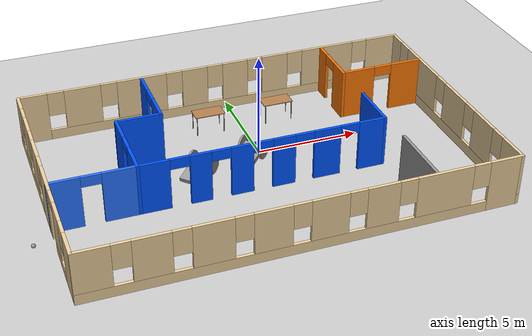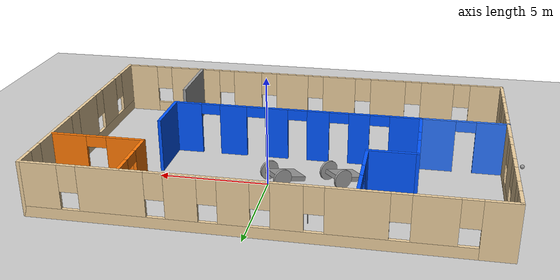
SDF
<sdf version="1.6">
 <world name="default">
  <plugin name="hello" filename="libhello.so"/>
  <light name="sun" type="directional">
   <pose>0 0 10 0 -0 0</pose>
   <diffuse>0.8 0.8 0.8 1</diffuse>
   <specular>0.2 0.2 0.2 1</specular>
   <attenuation>
    <range>1000</range>
    <constant>0.9</constant>
    <linear>0.01</linear>
    <quadratic>0.001</quadratic>
   </attenuation>
   <direction>-0.5 0.1 -0.9</direction>
  </light>
  <model name="ground_plane">
   <static>1</static>
   <link name="link">
    <collision name="collision">
     <geometry><plane><normal>0 0 1</normal><size>100 100</size></plane></geometry>
     <surface>
      <contact><collide_bitmask>65535</collide_bitmask></contact>
      <friction><ode><mu>100</mu><mu2>50</mu2></ode></friction>
     </surface>
    </collision>
    <visual name="visual">
     <cast_shadows>0</cast_shadows>
     <geometry><plane><normal>0 0 1</normal><size>100 100</size></plane></geometry>
     <material>
      <script><uri>file://media/materials/scripts/gazebo.material</uri><name>Gazebo/Grey</name></script>
     </material>
    </visual>
   </link>
  </model>
  <gravity>0 0 -9.8</gravity>
  <magnetic_field>6e-06 2.3e-05 -4.2e-05</magnetic_field>
  <atmosphere type="adiabatic"/>
  <physics name="default_physics" default="0" type="ode">
   <max_step_size>0.001</max_step_size>
   <real_time_factor>1</real_time_factor>
   <real_time_update_rate>1000</real_time_update_rate>
  </physics>
  <scene><ambient>0.4 0.4 0.4 1</ambient><background>0.7 0.7 0.7 1</background><shadows>1</shadows></scene>
  <spherical_coordinates>
   <surface_model>EARTH_WGS84</surface_model>
   <latitude_deg>0</latitude_deg>
   <longitude_deg>0</longitude_deg>
   <elevation>0</elevation>
   <heading_deg>0</heading_deg>
  </spherical_coordinates>
  <model name="MyNewOffice">
   <pose>-0.570202 -1.58607 0 0 -0 0</pose>
   <link name="Wall_1">
    <pose>0.005308 6.175 0 0 0 -7e-06</pose>
    <visual name="Wall_1_Visual_0">
     <pose>-9.16553 0 1.25 0 -0 0</pose>
     <geometry><box><size>1.41894 0.15 2.5</size></box></geometry>
     <material>
      <script><uri>file://media/materials/scripts/gazebo.material</uri><name>Gazebo/Grey</name></script>
      <ambient>0.921569 0.807843 0.615686 1</ambient>
     </material>
     <meta><layer>0</layer></meta>
    </visual>
    <collision name="Wall_1_Collision_0">
     <geometry><box><size>1.41894 0.15 2.5</size></box></geometry>
     <pose>-9.16553 0 1.25 0 -0 0</pose>
    </collision>
    <visual name="Wall_1_Visual_1">
     <pose>0.709472 0 0.25 0 -0 0</pose>
     <geometry><box><size>18.3311 0.15 0.5</size></box></geometry>
     <material>
      <script><uri>file://media/materials/scripts/gazebo.material</uri><name>Gazebo/Grey</name></script>
      <ambient>0.921569 0.807843 0.615686 1</ambient>
     </material>
     <meta><layer>0</layer></meta>
    </visual>
    <collision name="Wall_1_Collision_1">
     <geometry><box><size>18.3311 0.15 0.5</size></box></geometry>
     <pose>0.709472 0 0.25 0 -0 0</pose>
    </collision>
    <visual name="Wall_1_Visual_2">
     <pose>-6.76938 0 1.5 0 -0 0</pose>
     <geometry><box><size>1.77334 0.15 2</size></box></geometry>
     <material>
      <script><uri>file://media/materials/scripts/gazebo.material</uri><name>Gazebo/Grey</name></script>
      <ambient>0.921569 0.807843 0.615686 1</ambient>
     </material>
     <meta><layer>0</layer></meta>
    </visual>
    <collision name="Wall_1_Collision_2">
     <geometry><box><size>1.77334 0.15 2</size></box></geometry>
     <pose>-6.76938 0 1.5 0 -0 0</pose>
    </collision>
    <visual name="Wall_1_Visual_3">
     <pose>-3.84513 0 1.5 0 -0 0</pose>
     <geometry><box><size>2.47517 0.15 2</size></box></geometry>
     <material>
      <script><uri>file://media/materials/scripts/gazebo.material</uri><name>Gazebo/Grey</name></script>
      <ambient>0.921569 0.807843 0.615686 1</ambient>
     </material>
     <meta><layer>0</layer></meta>
    </visual>
    <collision name="Wall_1_Collision_3">
     <geometry><box><size>2.47517 0.15 2</size></box></geometry>
     <pose>-3.84513 0 1.5 0 -0 0</pose>
    </collision>
    <visual name="Wall_1_Visual_4">
     <pose>-1.15481 0 1.5 0 -0 0</pose>
     <geometry><box><size>1.30546 0.15 2</size></box></geometry>
     <material>
      <script><uri>file://media/materials/scripts/gazebo.material</uri><name>Gazebo/Grey</name></script>
      <ambient>0.921569 0.807843 0.615686 1</ambient>
     </material>
     <meta><layer>0</layer></meta>
    </visual>
    <collision name="Wall_1_Collision_4">
     <geometry><box><size>1.30546 0.15 2</size></box></geometry>
     <pose>-1.15481 0 1.5 0 -0 0</pose>
    </collision>
    <visual name="Wall_1_Visual_5">
     <pose>0.950655 0 1.5 0 -0 0</pose>
     <geometry><box><size>1.30547 0.15 2</size></box></geometry>
     <material>
      <script><uri>file://media/materials/scripts/gazebo.material</uri><name>Gazebo/Grey</name></script>
      <ambient>0.921569 0.807843 0.615686 1</ambient>
     </material>
     <meta><layer>0</layer></meta>
    </visual>
    <collision name="Wall_1_Collision_5">
     <geometry><box><size>1.30547 0.15 2</size></box></geometry>
     <pose>0.950655 0 1.5 0 -0 0</pose>
    </collision>
    <visual name="Wall_1_Visual_6">
     <pose>3.07951 0 1.5 0 -0 0</pose>
     <geometry><box><size>1.35225 0.15 2</size></box></geometry>
     <material>
      <script><uri>file://media/materials/scripts/gazebo.material</uri><name>Gazebo/Grey</name></script>
      <ambient>0.921569 0.807843 0.615686 1</ambient>
     </material>
     <meta><layer>0</layer></meta>
    </visual>
    <collision name="Wall_1_Collision_6">
     <geometry><box><size>1.35225 0.15 2</size></box></geometry>
     <pose>3.07951 0 1.5 0 -0 0</pose>
    </collision>
    <visual name="Wall_1_Visual_7">
     <pose>5.95698 0 1.5 0 -0 0</pose>
     <geometry><box><size>2.80268 0.15 2</size></box></geometry>
     <material>
      <script><uri>file://media/materials/scripts/gazebo.material</uri><name>Gazebo/Grey</name></script>
      <ambient>0.921569 0.807843 0.615686 1</ambient>
     </material>
     <meta><layer>0</layer></meta>
    </visual>
    <collision name="Wall_1_Collision_7">
     <geometry><box><size>2.80268 0.15 2</size></box></geometry>
     <pose>5.95698 0 1.5 0 -0 0</pose>
    </collision>
    <visual name="Wall_1_Visual_8">
     <pose>9.01666 0 1.5 0 -0 0</pose>
     <geometry><box><size>1.71668 0.15 2</size></box></geometry>
     <material>
      <script><uri>file://media/materials/scripts/gazebo.material</uri><name>Gazebo/Grey</name></script>
      <ambient>0.921569 0.807843 0.615686 1</ambient>
     </material>
     <meta><layer>0</layer></meta>
    </visual>
    <collision name="Wall_1_Collision_8">
     <geometry><box><size>1.71668 0.15 2</size></box></geometry>
     <pose>9.01666 0 1.5 0 -0 0</pose>
    </collision>
    <visual name="Wall_1_Visual_9">
     <pose>-8.05606 0 1.9 0 -0 0</pose>
     <geometry><box><size>0.8 0.15 1.2</size></box></geometry>
     <material>
      <script><uri>file://media/materials/scripts/gazebo.material</uri><name>Gazebo/Grey</name></script>
      <ambient>0.921569 0.807843 0.615686 1</ambient>
     </material>
     <meta><layer>0</layer></meta>
    </visual>
    <collision name="Wall_1_Collision_9">
     <geometry><box><size>0.8 0.15 1.2</size></box></geometry>
     <pose>-8.05606 0 1.9 0 -0 0</pose>
    </collision>
    <visual name="Wall_1_Visual_10">
     <pose>-5.48271 0 1.9 0 -0 0</pose>
     <geometry><box><size>0.8 0.15 1.2</size></box></geometry>
     <material>
      <script><uri>file://media/materials/scripts/gazebo.material</uri><name>Gazebo/Grey</name></script>
      <ambient>0.921569 0.807843 0.615686 1</ambient>
     </material>
     <meta><layer>0</layer></meta>
    </visual>
    <collision name="Wall_1_Collision_10">
     <geometry><box><size>0.8 0.15 1.2</size></box></geometry>
     <pose>-5.48271 0 1.9 0 -0 0</pose>
    </collision>
    <visual name="Wall_1_Visual_11">
     <pose>-2.20754 0 1.9 0 -0 0</pose>
     <geometry><box><size>0.8 0.15 1.2</size></box></geometry>
     <material>
      <script><uri>file://media/materials/scripts/gazebo.material</uri><name>Gazebo/Grey</name></script>
      <ambient>0.921569 0.807843 0.615686 1</ambient>
     </material>
     <meta><layer>0</layer></meta>
    </visual>
    <collision name="Wall_1_Collision_11">
     <geometry><box><size>0.8 0.15 1.2</size></box></geometry>
     <pose>-2.20754 0 1.9 0 -0 0</pose>
    </collision>
    <visual name="Wall_1_Visual_12">
     <pose>-0.102078 0 1.9 0 -0 0</pose>
     <geometry><box><size>0.8 0.15 1.2</size></box></geometry>
     <material>
      <script><uri>file://media/materials/scripts/gazebo.material</uri><name>Gazebo/Grey</name></script>
      <ambient>0.921569 0.807843 0.615686 1</ambient>
     </material>
     <meta><layer>0</layer></meta>
    </visual>
    <collision name="Wall_1_Collision_12">
     <geometry><box><size>0.8 0.15 1.2</size></box></geometry>
     <pose>-0.102078 0 1.9 0 -0 0</pose>
    </collision>
    <visual name="Wall_1_Visual_13">
     <pose>2.00339 0 1.9 0 -0 0</pose>
     <geometry><box><size>0.8 0.15 1.2</size></box></geometry>
     <material>
      <script><uri>file://media/materials/scripts/gazebo.material</uri><name>Gazebo/Grey</name></script>
      <ambient>0.921569 0.807843 0.615686 1</ambient>
     </material>
     <meta><layer>0</layer></meta>
    </visual>
    <collision name="Wall_1_Collision_13">
     <geometry><box><size>0.8 0.15 1.2</size></box></geometry>
     <pose>2.00339 0 1.9 0 -0 0</pose>
    </collision>
    <visual name="Wall_1_Visual_14">
     <pose>4.15564 0 1.9 0 -0 0</pose>
     <geometry><box><size>0.8 0.15 1.2</size></box></geometry>
     <material>
      <script><uri>file://media/materials/scripts/gazebo.material</uri><name>Gazebo/Grey</name></script>
      <ambient>0.921569 0.807843 0.615686 1</ambient>
     </material>
     <meta><layer>0</layer></meta>
    </visual>
    <collision name="Wall_1_Collision_14">
     <geometry><box><size>0.8 0.15 1.2</size></box></geometry>
     <pose>4.15564 0 1.9 0 -0 0</pose>
    </collision>
    <visual name="Wall_1_Visual_15">
     <pose>7.75832 0 1.9 0 -0 0</pose>
     <geometry><box><size>0.8 0.15 1.2</size></box></geometry>
     <material>
      <script><uri>file://media/materials/scripts/gazebo.material</uri><name>Gazebo/Grey</name></script>
      <ambient>0.921569 0.807843 0.615686 1</ambient>
     </material>
     <meta><layer>0</layer></meta>
    </visual>
    <collision name="Wall_1_Collision_15">
     <geometry><box><size>0.8 0.15 1.2</size></box></geometry>
     <pose>7.75832 0 1.9 0 -0 0</pose>
    </collision>
   </link>
   <link name="Wall_13">
    <pose>-3.85542 4.35663 0 0 0 -1.5708</pose>
    <visual name="Wall_13_Visual_0">
     <pose>-1.22116 0 1.25 0 -0 0</pose>
     <geometry><box><size>1.30769 0.15 2.5</size></box></geometry>
     <material>
      <script><uri>file://media/materials/scripts/gazebo.material</uri><name>Gazebo/Grey</name></script>
      <ambient>0 0.333333 1 1</ambient>
     </material>
     <meta><layer>0</layer></meta>
    </visual>
    <collision name="Wall_13_Collision_0">
     <geometry><box><size>1.30769 0.15 2.5</size></box></geometry>
     <pose>-1.22116 0 1.25 0 -0 0</pose>
    </collision>
    <visual name="Wall_13_Visual_1">
     <pose>1.10384 0 1.25 0 -0 0</pose>
     <geometry><box><size>1.54231 0.15 2.5</size></box></geometry>
     <material>
      <script><uri>file://media/materials/scripts/gazebo.material</uri><name>Gazebo/Grey</name></script>
      <ambient>0 0.333333 1 1</ambient>
     </material>
     <meta><layer>0</layer></meta>
    </visual>
    <collision name="Wall_13_Collision_1">
     <geometry><box><size>1.54231 0.15 2.5</size></box></geometry>
     <pose>1.10384 0 1.25 0 -0 0</pose>
    </collision>
    <visual name="Wall_13_Visual_2">
     <pose>-0.117314 0 2.25 0 -0 0</pose>
     <geometry><box><size>0.9 0.15 0.5</size></box></geometry>
     <material>
      <script><uri>file://media/materials/scripts/gazebo.material</uri><name>Gazebo/Grey</name></script>
      <ambient>0 0.333333 1 1</ambient>
     </material>
     <meta><layer>0</layer></meta>
    </visual>
    <collision name="Wall_13_Collision_2">
     <geometry><box><size>0.9 0.15 0.5</size></box></geometry>
     <pose>-0.117314 0 2.25 0 -0 0</pose>
    </collision>
   </link>
   <link name="Wall_14">
    <collision name="Wall_14_Collision">
     <geometry><box><size>2.25 0.15 2.5</size></box></geometry>
     <pose>0 0 1.25 0 -0 0</pose>
    </collision>
    <visual name="Wall_14_Visual">
     <pose>0 0 1.25 0 -0 0</pose>
     <geometry><box><size>2.25 0.15 2.5</size></box></geometry>
     <material>
      <script><uri>file://media/materials/scripts/gazebo.material</uri><name>Gazebo/Grey</name></script>
      <ambient>0 0.333333 1 1</ambient>
     </material>
     <meta><layer>0</layer></meta>
    </visual>
    <pose>-4.90542 2.55662 0 0 -0 3.14159</pose>
   </link>
   <link name="Wall_15">
    <pose>-5.95542 0.631625 0 0 0 -1.5708</pose>
    <visual name="Wall_15_Visual_0">
     <pose>-1.2711 0 1.25 0 -0 0</pose>
     <geometry><box><size>1.45781 0.15 2.5</size></box></geometry>
     <material>
      <script><uri>file://media/materials/scripts/gazebo.material</uri><name>Gazebo/Grey</name></script>
      <ambient>0 0.333333 1 1</ambient>
     </material>
     <meta><layer>0</layer></meta>
    </visual>
    <collision name="Wall_15_Collision_0">
     <geometry><box><size>1.45781 0.15 2.5</size></box></geometry>
     <pose>-1.2711 0 1.25 0 -0 0</pose>
    </collision>
    <visual name="Wall_15_Visual_1">
     <pose>1.17891 0 1.25 0 -0 0</pose>
     <geometry><box><size>1.64219 0.15 2.5</size></box></geometry>
     <material>
      <script><uri>file://media/materials/scripts/gazebo.material</uri><name>Gazebo/Grey</name></script>
      <ambient>0 0.333333 1 1</ambient>
     </material>
     <meta><layer>0</layer></meta>
    </visual>
    <collision name="Wall_15_Collision_1">
     <geometry><box><size>1.64219 0.15 2.5</size></box></geometry>
     <pose>1.17891 0 1.25 0 -0 0</pose>
    </collision>
    <visual name="Wall_15_Visual_2">
     <pose>-0.09219 0 2.25 0 -0 0</pose>
     <geometry><box><size>0.9 0.15 0.5</size></box></geometry>
     <material>
      <script><uri>file://media/materials/scripts/gazebo.material</uri><name>Gazebo/Grey</name></script>
      <ambient>0 0.333333 1 1</ambient>
     </material>
     <meta><layer>0</layer></meta>
    </visual>
    <collision name="Wall_15_Collision_2">
     <geometry><box><size>0.9 0.15 0.5</size></box></geometry>
     <pose>-0.09219 0 2.25 0 -0 0</pose>
    </collision>
   </link>
   <link name="Wall_16">
    <pose>-0.155416 -1.29337 0 0 -0 0</pose>
    <visual name="Wall_16_Visual_0">
     <pose>-5.12972 0 1.25 0 -0 0</pose>
     <geometry><box><size>1.49057 0.15 2.5</size></box></geometry>
     <material>
      <script><uri>file://media/materials/scripts/gazebo.material</uri><name>Gazebo/Grey</name></script>
      <ambient>0 0.333333 1 1</ambient>
     </material>
     <meta><layer>0</layer></meta>
    </visual>
    <collision name="Wall_16_Collision_0">
     <geometry><box><size>1.49057 0.15 2.5</size></box></geometry>
     <pose>-5.12972 0 1.25 0 -0 0</pose>
    </collision>
    <visual name="Wall_16_Visual_1">
     <pose>-2.9969 0 1.25 0 -0 0</pose>
     <geometry><box><size>0.975062 0.15 2.5</size></box></geometry>
     <material>
      <script><uri>file://media/materials/scripts/gazebo.material</uri><name>Gazebo/Grey</name></script>
      <ambient>0 0.333333 1 1</ambient>
     </material>
     <meta><layer>0</layer></meta>
    </visual>
    <collision name="Wall_16_Collision_1">
     <geometry><box><size>0.975062 0.15 2.5</size></box></geometry>
     <pose>-2.9969 0 1.25 0 -0 0</pose>
    </collision>
    <visual name="Wall_16_Visual_2">
     <pose>-1.08646 0 1.25 0 -0 0</pose>
     <geometry><box><size>1.04582 0.15 2.5</size></box></geometry>
     <material>
      <script><uri>file://media/materials/scripts/gazebo.material</uri><name>Gazebo/Grey</name></script>
      <ambient>0 0.333333 1 1</ambient>
     </material>
     <meta><layer>0</layer></meta>
    </visual>
    <collision name="Wall_16_Collision_2">
     <geometry><box><size>1.04582 0.15 2.5</size></box></geometry>
     <pose>-1.08646 0 1.25 0 -0 0</pose>
    </collision>
    <visual name="Wall_16_Visual_3">
     <pose>0.877051 0 1.25 0 -0 0</pose>
     <geometry><box><size>1.0812 0.15 2.5</size></box></geometry>
     <material>
      <script><uri>file://media/materials/scripts/gazebo.material</uri><name>Gazebo/Grey</name></script>
      <ambient>0 0.333333 1 1</ambient>
     </material>
     <meta><layer>0</layer></meta>
    </visual>
    <collision name="Wall_16_Collision_3">
     <geometry><box><size>1.0812 0.15 2.5</size></box></geometry>
     <pose>0.877051 0 1.25 0 -0 0</pose>
    </collision>
    <visual name="Wall_16_Visual_4">
     <pose>2.96438 0 1.25 0 -0 0</pose>
     <geometry><box><size>1.29347 0.15 2.5</size></box></geometry>
     <material>
      <script><uri>file://media/materials/scripts/gazebo.material</uri><name>Gazebo/Grey</name></script>
      <ambient>0 0.333333 1 1</ambient>
     </material>
     <meta><layer>0</layer></meta>
    </visual>
    <collision name="Wall_16_Collision_4">
     <geometry><box><size>1.29347 0.15 2.5</size></box></geometry>
     <pose>2.96438 0 1.25 0 -0 0</pose>
    </collision>
    <visual name="Wall_16_Visual_5">
     <pose>5.19306 0 1.25 0 -0 0</pose>
     <geometry><box><size>1.36388 0.15 2.5</size></box></geometry>
     <material>
      <script><uri>file://media/materials/scripts/gazebo.material</uri><name>Gazebo/Grey</name></script>
      <ambient>0 0.333333 1 1</ambient>
     </material>
     <meta><layer>0</layer></meta>
    </visual>
    <collision name="Wall_16_Collision_5">
     <geometry><box><size>1.36388 0.15 2.5</size></box></geometry>
     <pose>5.19306 0 1.25 0 -0 0</pose>
    </collision>
    <visual name="Wall_16_Visual_6">
     <pose>-3.93443 0 2.25 0 -0 0</pose>
     <geometry><box><size>0.9 0.15 0.5</size></box></geometry>
     <material>
      <script><uri>file://media/materials/scripts/gazebo.material</uri><name>Gazebo/Grey</name></script>
      <ambient>0 0.333333 1 1</ambient>
     </material>
     <meta><layer>0</layer></meta>
    </visual>
    <collision name="Wall_16_Collision_6">
     <geometry><box><size>0.9 0.15 0.5</size></box></geometry>
     <pose>-3.93443 0 2.25 0 -0 0</pose>
    </collision>
    <visual name="Wall_16_Visual_7">
     <pose>-2.05937 0 2.25 0 -0 0</pose>
     <geometry><box><size>0.9 0.15 0.5</size></box></geometry>
     <material>
      <script><uri>file://media/materials/scripts/gazebo.material</uri><name>Gazebo/Grey</name></script>
      <ambient>0 0.333333 1 1</ambient>
     </material>
     <meta><layer>0</layer></meta>
    </visual>
    <collision name="Wall_16_Collision_7">
     <geometry><box><size>0.9 0.15 0.5</size></box></geometry>
     <pose>-2.05937 0 2.25 0 -0 0</pose>
    </collision>
    <visual name="Wall_16_Visual_8">
     <pose>-0.113548 0 2.25 0 -0 0</pose>
     <geometry><box><size>0.9 0.15 0.5</size></box></geometry>
     <material>
      <script><uri>file://media/materials/scripts/gazebo.material</uri><name>Gazebo/Grey</name></script>
      <ambient>0 0.333333 1 1</ambient>
     </material>
     <meta><layer>0</layer></meta>
    </visual>
    <collision name="Wall_16_Collision_8">
     <geometry><box><size>0.9 0.15 0.5</size></box></geometry>
     <pose>-0.113548 0 2.25 0 -0 0</pose>
    </collision>
    <visual name="Wall_16_Visual_9">
     <pose>1.86765 0 2.25 0 -0 0</pose>
     <geometry><box><size>0.9 0.15 0.5</size></box></geometry>
     <material>
      <script><uri>file://media/materials/scripts/gazebo.material</uri><name>Gazebo/Grey</name></script>
      <ambient>0 0.333333 1 1</ambient>
     </material>
     <meta><layer>0</layer></meta>
    </visual>
    <collision name="Wall_16_Collision_9">
     <geometry><box><size>0.9 0.15 0.5</size></box></geometry>
     <pose>1.86765 0 2.25 0 -0 0</pose>
    </collision>
    <visual name="Wall_16_Visual_10">
     <pose>4.06112 0 2.25 0 -0 0</pose>
     <geometry><box><size>0.9 0.15 0.5</size></box></geometry>
     <material>
      <script><uri>file://media/materials/scripts/gazebo.material</uri><name>Gazebo/Grey</name></script>
      <ambient>0 0.333333 1 1</ambient>
     </material>
     <meta><layer>0</layer></meta>
    </visual>
    <collision name="Wall_16_Collision_10">
     <geometry><box><size>0.9 0.15 0.5</size></box></geometry>
     <pose>4.06112 0 2.25 0 -0 0</pose>
    </collision>
   </link>
   <link name="Wall_17">
    <collision name="Wall_17_Collision">
     <geometry><box><size>2.5 0.15 2.5</size></box></geometry>
     <pose>0 0 1.25 0 -0 0</pose>
    </collision>
    <visual name="Wall_17_Visual">
     <pose>0 0 1.25 0 -0 0</pose>
     <geometry><box><size>2.5 0.15 2.5</size></box></geometry>
     <material>
      <script><uri>file://media/materials/scripts/gazebo.material</uri><name>Gazebo/Grey</name></script>
      <ambient>0 0.333333 1 1</ambient>
     </material>
     <meta><layer>0</layer></meta>
    </visual>
    <pose>5.64458 -0.118375 0 0 -0 1.5708</pose>
   </link>
   <link name="Wall_2">
    <pose>9.80541 -6.5e-05 0 0 0 -1.5708</pose>
    <visual name="Wall_2_Visual_0">
     <pose>-5.73242 0 1.25 0 -0 0</pose>
     <geometry><box><size>1.03516 0.15 2.5</size></box></geometry>
     <material>
      <script><uri>file://media/materials/scripts/gazebo.material</uri><name>Gazebo/Grey</name></script>
      <ambient>0.921569 0.807843 0.615686 1</ambient>
     </material>
     <meta><layer>0</layer></meta>
    </visual>
    <collision name="Wall_2_Collision_0">
     <geometry><box><size>1.03516 0.15 2.5</size></box></geometry>
     <pose>-5.73242 0 1.25 0 -0 0</pose>
    </collision>
    <visual name="Wall_2_Visual_1">
     <pose>0.517579 0 0.25 0 -0 0</pose>
     <geometry><box><size>11.4648 0.15 0.5</size></box></geometry>
     <material>
      <script><uri>file://media/materials/scripts/gazebo.material</uri><name>Gazebo/Grey</name></script>
      <ambient>0.921569 0.807843 0.615686 1</ambient>
     </material>
     <meta><layer>0</layer></meta>
    </visual>
    <collision name="Wall_2_Collision_1">
     <geometry><box><size>11.4648 0.15 0.5</size></box></geometry>
     <pose>0.517579 0 0.25 0 -0 0</pose>
    </collision>
    <visual name="Wall_2_Visual_2">
     <pose>-2.89653 0 1.5 0 -0 0</pose>
     <geometry><box><size>3.03662 0.15 2</size></box></geometry>
     <material>
      <script><uri>file://media/materials/scripts/gazebo.material</uri><name>Gazebo/Grey</name></script>
      <ambient>0.921569 0.807843 0.615686 1</ambient>
     </material>
     <meta><layer>0</layer></meta>
    </visual>
    <collision name="Wall_2_Collision_2">
     <geometry><box><size>3.03662 0.15 2</size></box></geometry>
     <pose>-2.89653 0 1.5 0 -0 0</pose>
    </collision>
    <visual name="Wall_2_Visual_3">
     <pose>0.402032 0 1.5 0 -0 0</pose>
     <geometry><box><size>1.9605 0.15 2</size></box></geometry>
     <material>
      <script><uri>file://media/materials/scripts/gazebo.material</uri><name>Gazebo/Grey</name></script>
      <ambient>0.921569 0.807843 0.615686 1</ambient>
     </material>
     <meta><layer>0</layer></meta>
    </visual>
    <collision name="Wall_2_Collision_3">
     <geometry><box><size>1.9605 0.15 2</size></box></geometry>
     <pose>0.402032 0 1.5 0 -0 0</pose>
    </collision>
    <visual name="Wall_2_Visual_4">
     <pose>3.02217 0 1.5 0 -0 0</pose>
     <geometry><box><size>1.67977 0.15 2</size></box></geometry>
     <material>
      <script><uri>file://media/materials/scripts/gazebo.material</uri><name>Gazebo/Grey</name></script>
      <ambient>0.921569 0.807843 0.615686 1</ambient>
     </material>
     <meta><layer>0</layer></meta>
    </visual>
    <collision name="Wall_2_Collision_4">
     <geometry><box><size>1.67977 0.15 2</size></box></geometry>
     <pose>3.02217 0 1.5 0 -0 0</pose>
    </collision>
    <visual name="Wall_2_Visual_5">
     <pose>5.45603 0 1.5 0 -0 0</pose>
     <geometry><box><size>1.58795 0.15 2</size></box></geometry>
     <material>
      <script><uri>file://media/materials/scripts/gazebo.material</uri><name>Gazebo/Grey</name></script>
      <ambient>0.921569 0.807843 0.615686 1</ambient>
     </material>
     <meta><layer>0</layer></meta>
    </visual>
    <collision name="Wall_2_Collision_5">
     <geometry><box><size>1.58795 0.15 2</size></box></geometry>
     <pose>5.45603 0 1.5 0 -0 0</pose>
    </collision>
    <visual name="Wall_2_Visual_6">
     <pose>-4.81484 0 1.9 0 -0 0</pose>
     <geometry><box><size>0.8 0.15 1.2</size></box></geometry>
     <material>
      <script><uri>file://media/materials/scripts/gazebo.material</uri><name>Gazebo/Grey</name></script>
      <ambient>0.921569 0.807843 0.615686 1</ambient>
     </material>
     <meta><layer>0</layer></meta>
    </visual>
    <collision name="Wall_2_Collision_6">
     <geometry><box><size>0.8 0.15 1.2</size></box></geometry>
     <pose>-4.81484 0 1.9 0 -0 0</pose>
    </collision>
    <visual name="Wall_2_Visual_7">
     <pose>-0.978217 0 1.9 0 -0 0</pose>
     <geometry><box><size>0.8 0.15 1.2</size></box></geometry>
     <material>
      <script><uri>file://media/materials/scripts/gazebo.material</uri><name>Gazebo/Grey</name></script>
      <ambient>0.921569 0.807843 0.615686 1</ambient>
     </material>
     <meta><layer>0</layer></meta>
    </visual>
    <collision name="Wall_2_Collision_7">
     <geometry><box><size>0.8 0.15 1.2</size></box></geometry>
     <pose>-0.978217 0 1.9 0 -0 0</pose>
    </collision>
    <visual name="Wall_2_Visual_8">
     <pose>1.78228 0 1.9 0 -0 0</pose>
     <geometry><box><size>0.8 0.15 1.2</size></box></geometry>
     <material>
      <script><uri>file://media/materials/scripts/gazebo.material</uri><name>Gazebo/Grey</name></script>
      <ambient>0.921569 0.807843 0.615686 1</ambient>
     </material>
     <meta><layer>0</layer></meta>
    </visual>
    <collision name="Wall_2_Collision_8">
     <geometry><box><size>0.8 0.15 1.2</size></box></geometry>
     <pose>1.78228 0 1.9 0 -0 0</pose>
    </collision>
    <visual name="Wall_2_Visual_9">
     <pose>4.26205 0 1.9 0 -0 0</pose>
     <geometry><box><size>0.8 0.15 1.2</size></box></geometry>
     <material>
      <script><uri>file://media/materials/scripts/gazebo.material</uri><name>Gazebo/Grey</name></script>
      <ambient>0.921569 0.807843 0.615686 1</ambient>
     </material>
     <meta><layer>0</layer></meta>
    </visual>
    <collision name="Wall_2_Collision_9">
     <geometry><box><size>0.8 0.15 1.2</size></box></geometry>
     <pose>4.26205 0 1.9 0 -0 0</pose>
    </collision>
   </link>
   <link name="Wall_20">
    <pose>5.61119 4.69117 0 0 0 -1.5708</pose>
    <visual name="Wall_20_Visual_0">
     <pose>-1.0368 0 1.25 0 -0 0</pose>
     <geometry><box><size>0.926393 0.15 2.5</size></box></geometry>
     <material>
      <script><uri>file://media/materials/scripts/gazebo.material</uri><name>Gazebo/Grey</name></script>
      <ambient>0.996078 0.47451 0.0196078 1</ambient>
     </material>
     <meta><layer>0</layer></meta>
    </visual>
    <collision name="Wall_20_Collision_0">
     <geometry><box><size>0.926393 0.15 2.5</size></box></geometry>
     <pose>-1.0368 0 1.25 0 -0 0</pose>
    </collision>
    <visual name="Wall_20_Visual_1">
     <pose>0.913196 0 1.25 0 -0 0</pose>
     <geometry><box><size>1.17361 0.15 2.5</size></box></geometry>
     <material>
      <script><uri>file://media/materials/scripts/gazebo.material</uri><name>Gazebo/Grey</name></script>
      <ambient>0.996078 0.47451 0.0196078 1</ambient>
     </material>
     <meta><layer>0</layer></meta>
    </visual>
    <collision name="Wall_20_Collision_1">
     <geometry><box><size>1.17361 0.15 2.5</size></box></geometry>
     <pose>0.913196 0 1.25 0 -0 0</pose>
    </collision>
    <visual name="Wall_20_Visual_2">
     <pose>-0.123607 0 2.25 0 -0 0</pose>
     <geometry><box><size>0.9 0.15 0.5</size></box></geometry>
     <material>
      <script><uri>file://media/materials/scripts/gazebo.material</uri><name>Gazebo/Grey</name></script>
      <ambient>0.996078 0.47451 0.0196078 1</ambient>
     </material>
     <meta><layer>0</layer></meta>
    </visual>
    <collision name="Wall_20_Collision_2">
     <geometry><box><size>0.9 0.15 0.5</size></box></geometry>
     <pose>-0.123607 0 2.25 0 -0 0</pose>
    </collision>
   </link>
   <link name="Wall_21">
    <pose>7.66119 3.26617 0 0 -0 0</pose>
    <visual name="Wall_21_Visual_0">
     <pose>-1.25967 0 1.25 0 -0 0</pose>
     <geometry><box><size>1.73065 0.15 2.5</size></box></geometry>
     <material>
      <script><uri>file://media/materials/scripts/gazebo.material</uri><name>Gazebo/Grey</name></script>
      <ambient>0.996078 0.47451 0.0196078 1</ambient>
     </material>
     <meta><layer>0</layer></meta>
    </visual>
    <collision name="Wall_21_Collision_0">
     <geometry><box><size>1.73065 0.15 2.5</size></box></geometry>
     <pose>-1.25967 0 1.25 0 -0 0</pose>
    </collision>
    <visual name="Wall_21_Visual_1">
     <pose>1.31533 0 1.25 0 -0 0</pose>
     <geometry><box><size>1.61935 0.15 2.5</size></box></geometry>
     <material>
      <script><uri>file://media/materials/scripts/gazebo.material</uri><name>Gazebo/Grey</name></script>
      <ambient>0.996078 0.47451 0.0196078 1</ambient>
     </material>
     <meta><layer>0</layer></meta>
    </visual>
    <collision name="Wall_21_Collision_1">
     <geometry><box><size>1.61935 0.15 2.5</size></box></geometry>
     <pose>1.31533 0 1.25 0 -0 0</pose>
    </collision>
    <visual name="Wall_21_Visual_2">
     <pose>0.055654 0 2.25 0 -0 0</pose>
     <geometry><box><size>0.9 0.15 0.5</size></box></geometry>
     <material>
      <script><uri>file://media/materials/scripts/gazebo.material</uri><name>Gazebo/Grey</name></script>
      <ambient>0.996078 0.47451 0.0196078 1</ambient>
     </material>
     <meta><layer>0</layer></meta>
    </visual>
    <collision name="Wall_21_Collision_2">
     <geometry><box><size>0.9 0.15 0.5</size></box></geometry>
     <pose>0.055654 0 2.25 0 -0 0</pose>
    </collision>
   </link>
   <link name="Wall_23">
    <collision name="Wall_23_Collision">
     <geometry><box><size>3.25 0.15 2.5</size></box></geometry>
     <pose>0 0 1.25 0 -0 0</pose>
    </collision>
    <visual name="Wall_23_Visual">
     <pose>0 0 1.25 0 -0 0</pose>
     <geometry><box><size>3.25 0.15 2.5</size></box></geometry>
     <material>
      <script><uri>file://media/materials/scripts/gazebo.material</uri><name>Gazebo/Grey</name></script>
      <ambient>1 1 1 1</ambient>
     </material>
     <meta><layer>0</layer></meta>
    </visual>
    <pose>5.74539 -4.58962 0 0 -0 1.5708</pose>
   </link>
   <link name="Wall_27">
    <pose>-7.88042 -1.29337 0 0 -0 3.14159</pose>
    <visual name="Wall_27_Visual_0">
     <pose>-1.18662 0 1.25 0 -0 0</pose>
     <geometry><box><size>1.62676 0.15 2.5</size></box></geometry>
     <material>
      <script><uri>file://media/materials/scripts/gazebo.material</uri><name>Gazebo/Grey</name></script>
      <ambient>0.160784 0.454902 1 1</ambient>
     </material>
     <meta><layer>0</layer></meta>
    </visual>
    <collision name="Wall_27_Collision_0">
     <geometry><box><size>1.62676 0.15 2.5</size></box></geometry>
     <pose>-1.18662 0 1.25 0 -0 0</pose>
    </collision>
    <visual name="Wall_27_Visual_1">
     <pose>1.26338 0 1.25 0 -0 0</pose>
     <geometry><box><size>1.47324 0.15 2.5</size></box></geometry>
     <material>
      <script><uri>file://media/materials/scripts/gazebo.material</uri><name>Gazebo/Grey</name></script>
      <ambient>0.160784 0.454902 1 1</ambient>
     </material>
     <meta><layer>0</layer></meta>
    </visual>
    <collision name="Wall_27_Collision_1">
     <geometry><box><size>1.47324 0.15 2.5</size></box></geometry>
     <pose>1.26338 0 1.25 0 -0 0</pose>
    </collision>
    <visual name="Wall_27_Visual_2">
     <pose>0.076756 0 2.25 0 -0 0</pose>
     <geometry><box><size>0.9 0.15 0.5</size></box></geometry>
     <material>
      <script><uri>file://media/materials/scripts/gazebo.material</uri><name>Gazebo/Grey</name></script>
      <ambient>0.160784 0.454902 1 1</ambient>
     </material>
     <meta><layer>0</layer></meta>
    </visual>
    <collision name="Wall_27_Collision_2">
     <geometry><box><size>0.9 0.15 0.5</size></box></geometry>
     <pose>0.076756 0 2.25 0 -0 0</pose>
    </collision>
   </link>
   <link name="Wall_3">
    <pose>0.005308 -6.175 0 0 -0 3.14159</pose>
    <visual name="Wall_3_Visual_0">
     <pose>-9.0635 0 1.25 0 -0 0</pose>
     <geometry><box><size>1.62321 0.15 2.5</size></box></geometry>
     <material>
      <script><uri>file://media/materials/scripts/gazebo.material</uri><name>Gazebo/Grey</name></script>
      <ambient>0.921569 0.807843 0.615686 1</ambient>
     </material>
     <meta><layer>0</layer></meta>
    </visual>
    <collision name="Wall_3_Collision_0">
     <geometry><box><size>1.62321 0.15 2.5</size></box></geometry>
     <pose>-9.0635 0 1.25 0 -0 0</pose>
    </collision>
    <visual name="Wall_3_Visual_1">
     <pose>0.811603 0 0.25 0 -0 0</pose>
     <geometry><box><size>18.127 0.15 0.5</size></box></geometry>
     <material>
      <script><uri>file://media/materials/scripts/gazebo.material</uri><name>Gazebo/Grey</name></script>
      <ambient>0.921569 0.807843 0.615686 1</ambient>
     </material>
     <meta><layer>0</layer></meta>
    </visual>
    <collision name="Wall_3_Collision_1">
     <geometry><box><size>18.127 0.15 0.5</size></box></geometry>
     <pose>0.811603 0 0.25 0 -0 0</pose>
    </collision>
    <visual name="Wall_3_Visual_2">
     <pose>-6.12074 0 1.5 0 -0 0</pose>
     <geometry><box><size>2.66232 0.15 2</size></box></geometry>
     <material>
      <script><uri>file://media/materials/scripts/gazebo.material</uri><name>Gazebo/Grey</name></script>
      <ambient>0.921569 0.807843 0.615686 1</ambient>
     </material>
     <meta><layer>0</layer></meta>
    </visual>
    <collision name="Wall_3_Collision_2">
     <geometry><box><size>2.66232 0.15 2</size></box></geometry>
     <pose>-6.12074 0 1.5 0 -0 0</pose>
    </collision>
    <visual name="Wall_3_Visual_3">
     <pose>-3.24327 0 1.5 0 -0 0</pose>
     <geometry><box><size>1.49262 0.15 2</size></box></geometry>
     <material>
      <script><uri>file://media/materials/scripts/gazebo.material</uri><name>Gazebo/Grey</name></script>
      <ambient>0.921569 0.807843 0.615686 1</ambient>
     </material>
     <meta><layer>0</layer></meta>
    </visual>
    <collision name="Wall_3_Collision_3">
     <geometry><box><size>1.49262 0.15 2</size></box></geometry>
     <pose>-3.24327 0 1.5 0 -0 0</pose>
    </collision>
    <visual name="Wall_3_Visual_4">
     <pose>-0.857078 0 1.5 0 -0 0</pose>
     <geometry><box><size>1.67977 0.15 2</size></box></geometry>
     <material>
      <script><uri>file://media/materials/scripts/gazebo.material</uri><name>Gazebo/Grey</name></script>
      <ambient>0.921569 0.807843 0.615686 1</ambient>
     </material>
     <meta><layer>0</layer></meta>
    </visual>
    <collision name="Wall_3_Collision_4">
     <geometry><box><size>1.67977 0.15 2</size></box></geometry>
     <pose>-0.857078 0 1.5 0 -0 0</pose>
    </collision>
    <visual name="Wall_3_Visual_5">
     <pose>1.62269 0 1.5 0 -0 0</pose>
     <geometry><box><size>1.67977 0.15 2</size></box></geometry>
     <material>
      <script><uri>file://media/materials/scripts/gazebo.material</uri><name>Gazebo/Grey</name></script>
      <ambient>0.921569 0.807843 0.615686 1</ambient>
     </material>
     <meta><layer>0</layer></meta>
    </visual>
    <collision name="Wall_3_Collision_5">
     <geometry><box><size>1.67977 0.15 2</size></box></geometry>
     <pose>1.62269 0 1.5 0 -0 0</pose>
    </collision>
    <visual name="Wall_3_Visual_6">
     <pose>4.14925 0 1.5 0 -0 0</pose>
     <geometry><box><size>1.77334 0.15 2</size></box></geometry>
     <material>
      <script><uri>file://media/materials/scripts/gazebo.material</uri><name>Gazebo/Grey</name></script>
      <ambient>0.921569 0.807843 0.615686 1</ambient>
     </material>
     <meta><layer>0</layer></meta>
    </visual>
    <collision name="Wall_3_Collision_6">
     <geometry><box><size>1.77334 0.15 2</size></box></geometry>
     <pose>4.14925 0 1.5 0 -0 0</pose>
    </collision>
    <visual name="Wall_3_Visual_7">
     <pose>6.65241 0 1.5 0 -0 0</pose>
     <geometry><box><size>1.63298 0.15 2</size></box></geometry>
     <material>
      <script><uri>file://media/materials/scripts/gazebo.material</uri><name>Gazebo/Grey</name></script>
      <ambient>0.921569 0.807843 0.615686 1</ambient>
     </material>
     <meta><layer>0</layer></meta>
    </visual>
    <collision name="Wall_3_Collision_7">
     <geometry><box><size>1.63298 0.15 2</size></box></geometry>
     <pose>6.65241 0 1.5 0 -0 0</pose>
    </collision>
    <visual name="Wall_3_Visual_8">
     <pose>9.07201 0 1.5 0 -0 0</pose>
     <geometry><box><size>1.6062 0.15 2</size></box></geometry>
     <material>
      <script><uri>file://media/materials/scripts/gazebo.material</uri><name>Gazebo/Grey</name></script>
      <ambient>0.921569 0.807843 0.615686 1</ambient>
     </material>
     <meta><layer>0</layer></meta>
    </visual>
    <collision name="Wall_3_Collision_8">
     <geometry><box><size>1.6062 0.15 2</size></box></geometry>
     <pose>9.07201 0 1.5 0 -0 0</pose>
    </collision>
    <visual name="Wall_3_Visual_9">
     <pose>-7.8519 0 1.9 0 -0 0</pose>
     <geometry><box><size>0.8 0.15 1.2</size></box></geometry>
     <material>
      <script><uri>file://media/materials/scripts/gazebo.material</uri><name>Gazebo/Grey</name></script>
      <ambient>0.921569 0.807843 0.615686 1</ambient>
     </material>
     <meta><layer>0</layer></meta>
    </visual>
    <collision name="Wall_3_Collision_9">
     <geometry><box><size>0.8 0.15 1.2</size></box></geometry>
     <pose>-7.8519 0 1.9 0 -0 0</pose>
    </collision>
    <visual name="Wall_3_Visual_10">
     <pose>-4.38958 0 1.9 0 -0 0</pose>
     <geometry><box><size>0.8 0.15 1.2</size></box></geometry>
     <material>
      <script><uri>file://media/materials/scripts/gazebo.material</uri><name>Gazebo/Grey</name></script>
      <ambient>0.921569 0.807843 0.615686 1</ambient>
     </material>
     <meta><layer>0</layer></meta>
    </visual>
    <collision name="Wall_3_Collision_10">
     <geometry><box><size>0.8 0.15 1.2</size></box></geometry>
     <pose>-4.38958 0 1.9 0 -0 0</pose>
    </collision>
    <visual name="Wall_3_Visual_11">
     <pose>-2.09696 0 1.9 0 -0 0</pose>
     <geometry><box><size>0.8 0.15 1.2</size></box></geometry>
     <material>
      <script><uri>file://media/materials/scripts/gazebo.material</uri><name>Gazebo/Grey</name></script>
      <ambient>0.921569 0.807843 0.615686 1</ambient>
     </material>
     <meta><layer>0</layer></meta>
    </visual>
    <collision name="Wall_3_Collision_11">
     <geometry><box><size>0.8 0.15 1.2</size></box></geometry>
     <pose>-2.09696 0 1.9 0 -0 0</pose>
    </collision>
    <visual name="Wall_3_Visual_12">
     <pose>0.382807 0 1.9 0 -0 0</pose>
     <geometry><box><size>0.8 0.15 1.2</size></box></geometry>
     <material>
      <script><uri>file://media/materials/scripts/gazebo.material</uri><name>Gazebo/Grey</name></script>
      <ambient>0.921569 0.807843 0.615686 1</ambient>
     </material>
     <meta><layer>0</layer></meta>
    </visual>
    <collision name="Wall_3_Collision_12">
     <geometry><box><size>0.8 0.15 1.2</size></box></geometry>
     <pose>0.382807 0 1.9 0 -0 0</pose>
    </collision>
    <visual name="Wall_3_Visual_13">
     <pose>2.86258 0 1.9 0 -0 0</pose>
     <geometry><box><size>0.8 0.15 1.2</size></box></geometry>
     <material>
      <script><uri>file://media/materials/scripts/gazebo.material</uri><name>Gazebo/Grey</name></script>
      <ambient>0.921569 0.807843 0.615686 1</ambient>
     </material>
     <meta><layer>0</layer></meta>
    </visual>
    <collision name="Wall_3_Collision_13">
     <geometry><box><size>0.8 0.15 1.2</size></box></geometry>
     <pose>2.86258 0 1.9 0 -0 0</pose>
    </collision>
    <visual name="Wall_3_Visual_14">
     <pose>5.43592 0 1.9 0 -0 0</pose>
     <geometry><box><size>0.8 0.15 1.2</size></box></geometry>
     <material>
      <script><uri>file://media/materials/scripts/gazebo.material</uri><name>Gazebo/Grey</name></script>
      <ambient>0.921569 0.807843 0.615686 1</ambient>
     </material>
     <meta><layer>0</layer></meta>
    </visual>
    <collision name="Wall_3_Collision_14">
     <geometry><box><size>0.8 0.15 1.2</size></box></geometry>
     <pose>5.43592 0 1.9 0 -0 0</pose>
    </collision>
    <visual name="Wall_3_Visual_15">
     <pose>7.8689 0 1.9 0 -0 0</pose>
     <geometry><box><size>0.8 0.15 1.2</size></box></geometry>
     <material>
      <script><uri>file://media/materials/scripts/gazebo.material</uri><name>Gazebo/Grey</name></script>
      <ambient>0.921569 0.807843 0.615686 1</ambient>
     </material>
     <meta><layer>0</layer></meta>
    </visual>
    <collision name="Wall_3_Collision_15">
     <geometry><box><size>0.8 0.15 1.2</size></box></geometry>
     <pose>7.8689 0 1.9 0 -0 0</pose>
    </collision>
   </link>
   <link name="Wall_4">
    <pose>-9.7948 6.6e-05 0 0 -0 1.5708</pose>
    <visual name="Wall_4_Visual_0">
     <pose>-5.52624 0 1.25 0 -0 0</pose>
     <geometry><box><size>1.44739 0.15 2.5</size></box></geometry>
     <material>
      <script><uri>file://media/materials/scripts/gazebo.material</uri><name>Gazebo/Grey</name></script>
      <ambient>0.921569 0.807843 0.615686 1</ambient>
     </material>
     <meta><layer>0</layer></meta>
    </visual>
    <collision name="Wall_4_Collision_0">
     <geometry><box><size>1.44739 0.15 2.5</size></box></geometry>
     <pose>-5.52624 0 1.25 0 -0 0</pose>
    </collision>
    <visual name="Wall_4_Visual_1">
     <pose>-0.845043 0 1.25 0 -0 0</pose>
     <geometry><box><size>1.9105 0.15 2.5</size></box></geometry>
     <material>
      <script><uri>file://media/materials/scripts/gazebo.material</uri><name>Gazebo/Grey</name></script>
      <ambient>0.921569 0.807843 0.615686 1</ambient>
     </material>
     <meta><layer>0</layer></meta>
    </visual>
    <collision name="Wall_4_Collision_1">
     <geometry><box><size>1.9105 0.15 2.5</size></box></geometry>
     <pose>-0.845043 0 1.25 0 -0 0</pose>
    </collision>
    <visual name="Wall_4_Visual_2">
     <pose>-3.75142 0 0.25 0 -0 0</pose>
     <geometry><box><size>2.10225 0.15 0.5</size></box></geometry>
     <material>
      <script><uri>file://media/materials/scripts/gazebo.material</uri><name>Gazebo/Grey</name></script>
      <ambient>0.921569 0.807843 0.615686 1</ambient>
     </material>
     <meta><layer>0</layer></meta>
    </visual>
    <collision name="Wall_4_Collision_2">
     <geometry><box><size>2.10225 0.15 0.5</size></box></geometry>
     <pose>-3.75142 0 0.25 0 -0 0</pose>
    </collision>
    <visual name="Wall_4_Visual_3">
     <pose>3.18007 0 0.25 0 -0 0</pose>
     <geometry><box><size>6.13973 0.15 0.5</size></box></geometry>
     <material>
      <script><uri>file://media/materials/scripts/gazebo.material</uri><name>Gazebo/Grey</name></script>
      <ambient>0.921569 0.807843 0.615686 1</ambient>
     </material>
     <meta><layer>0</layer></meta>
    </visual>
    <collision name="Wall_4_Collision_3">
     <geometry><box><size>6.13973 0.15 0.5</size></box></geometry>
     <pose>3.18007 0 0.25 0 -0 0</pose>
    </collision>
    <visual name="Wall_4_Visual_4">
     <pose>-3.35142 0 1.5 0 -0 0</pose>
     <geometry><box><size>1.30225 0.15 2</size></box></geometry>
     <material>
      <script><uri>file://media/materials/scripts/gazebo.material</uri><name>Gazebo/Grey</name></script>
      <ambient>0.921569 0.807843 0.615686 1</ambient>
     </material>
     <meta><layer>0</layer></meta>
    </visual>
    <collision name="Wall_4_Collision_4">
     <geometry><box><size>1.30225 0.15 2</size></box></geometry>
     <pose>-3.35142 0 1.5 0 -0 0</pose>
    </collision>
    <visual name="Wall_4_Visual_5">
     <pose>-3.35142 0 1.5 0 -0 0</pose>
     <geometry><box><size>1.30225 0.15 2</size></box></geometry>
     <material>
      <script><uri>file://media/materials/scripts/gazebo.material</uri><name>Gazebo/Grey</name></script>
      <ambient>0.921569 0.807843 0.615686 1</ambient>
     </material>
     <meta><layer>0</layer></meta>
    </visual>
    <collision name="Wall_4_Collision_5">
     <geometry><box><size>1.30225 0.15 2</size></box></geometry>
     <pose>-3.35142 0 1.5 0 -0 0</pose>
    </collision>
    <visual name="Wall_4_Visual_6">
     <pose>1.60973 0 1.5 0 -0 0</pose>
     <geometry><box><size>1.39904 0.15 2</size></box></geometry>
     <material>
      <script><uri>file://media/materials/scripts/gazebo.material</uri><name>Gazebo/Grey</name></script>
      <ambient>0.921569 0.807843 0.615686 1</ambient>
     </material>
     <meta><layer>0</layer></meta>
    </visual>
    <collision name="Wall_4_Collision_6">
     <geometry><box><size>1.39904 0.15 2</size></box></geometry>
     <pose>1.60973 0 1.5 0 -0 0</pose>
    </collision>
    <visual name="Wall_4_Visual_7">
     <pose>3.73859 0 1.5 0 -0 0</pose>
     <geometry><box><size>1.25868 0.15 2</size></box></geometry>
     <material>
      <script><uri>file://media/materials/scripts/gazebo.material</uri><name>Gazebo/Grey</name></script>
      <ambient>0.921569 0.807843 0.615686 1</ambient>
     </material>
     <meta><layer>0</layer></meta>
    </visual>
    <collision name="Wall_4_Collision_7">
     <geometry><box><size>1.25868 0.15 2</size></box></geometry>
     <pose>3.73859 0 1.5 0 -0 0</pose>
    </collision>
    <visual name="Wall_4_Visual_8">
     <pose>5.70893 0 1.5 0 -0 0</pose>
     <geometry><box><size>1.08201 0.15 2</size></box></geometry>
     <material>
      <script><uri>file://media/materials/scripts/gazebo.material</uri><name>Gazebo/Grey</name></script>
      <ambient>0.921569 0.807843 0.615686 1</ambient>
     </material>
     <meta><layer>0</layer></meta>
    </visual>
    <collision name="Wall_4_Collision_8">
     <geometry><box><size>1.08201 0.15 2</size></box></geometry>
     <pose>5.70893 0 1.5 0 -0 0</pose>
    </collision>
    <visual name="Wall_4_Visual_9">
     <pose>-4.40254 0 1.9 0 -0 0</pose>
     <geometry><box><size>0.8 0.15 1.2</size></box></geometry>
     <material>
      <script><uri>file://media/materials/scripts/gazebo.material</uri><name>Gazebo/Grey</name></script>
      <ambient>0.921569 0.807843 0.615686 1</ambient>
     </material>
     <meta><layer>0</layer></meta>
    </visual>
    <collision name="Wall_4_Collision_9">
     <geometry><box><size>0.8 0.15 1.2</size></box></geometry>
     <pose>-4.40254 0 1.9 0 -0 0</pose>
    </collision>
    <visual name="Wall_4_Visual_10">
     <pose>0.510206 0 1.9 0 -0 0</pose>
     <geometry><box><size>0.8 0.15 1.2</size></box></geometry>
     <material>
      <script><uri>file://media/materials/scripts/gazebo.material</uri><name>Gazebo/Grey</name></script>
      <ambient>0.921569 0.807843 0.615686 1</ambient>
     </material>
     <meta><layer>0</layer></meta>
    </visual>
    <collision name="Wall_4_Collision_10">
     <geometry><box><size>0.8 0.15 1.2</size></box></geometry>
     <pose>0.510206 0 1.9 0 -0 0</pose>
    </collision>
    <visual name="Wall_4_Visual_11">
     <pose>2.70925 0 1.9 0 -0 0</pose>
     <geometry><box><size>0.8 0.15 1.2</size></box></geometry>
     <material>
      <script><uri>file://media/materials/scripts/gazebo.material</uri><name>Gazebo/Grey</name></script>
      <ambient>0.921569 0.807843 0.615686 1</ambient>
     </material>
     <meta><layer>0</layer></meta>
    </visual>
    <collision name="Wall_4_Collision_11">
     <geometry><box><size>0.8 0.15 1.2</size></box></geometry>
     <pose>2.70925 0 1.9 0 -0 0</pose>
    </collision>
    <visual name="Wall_4_Visual_12">
     <pose>4.76792 0 1.9 0 -0 0</pose>
     <geometry><box><size>0.8 0.15 1.2</size></box></geometry>
     <material>
      <script><uri>file://media/materials/scripts/gazebo.material</uri><name>Gazebo/Grey</name></script>
      <ambient>0.921569 0.807843 0.615686 1</ambient>
     </material>
     <meta><layer>0</layer></meta>
    </visual>
    <collision name="Wall_4_Collision_12">
     <geometry><box><size>0.8 0.15 1.2</size></box></geometry>
     <pose>4.76792 0 1.9 0 -0 0</pose>
    </collision>
    <visual name="Wall_4_Visual_13">
     <pose>-2.25029 0 2.25 0 -0 0</pose>
     <geometry><box><size>0.9 0.15 0.5</size></box></geometry>
     <material>
      <script><uri>file://media/materials/scripts/gazebo.material</uri><name>Gazebo/Grey</name></script>
      <ambient>0.921569 0.807843 0.615686 1</ambient>
     </material>
     <meta><layer>0</layer></meta>
    </visual>
    <collision name="Wall_4_Collision_13">
     <geometry><box><size>0.9 0.15 0.5</size></box></geometry>
     <pose>-2.25029 0 2.25 0 -0 0</pose>
    </collision>
    <visual name="Wall_4_Visual_14">
     <pose>-2.25029 0 2.25 0 -0 0</pose>
     <geometry><box><size>0.9 0.15 0.5</size></box></geometry>
     <material>
      <script><uri>file://media/materials/scripts/gazebo.material</uri><name>Gazebo/Grey</name></script>
      <ambient>0.921569 0.807843 0.615686 1</ambient>
     </material>
     <meta><layer>0</layer></meta>
    </visual>
    <collision name="Wall_4_Collision_14">
     <geometry><box><size>0.9 0.15 0.5</size></box></geometry>
     <pose>-2.25029 0 2.25 0 -0 0</pose>
    </collision>
   </link>
   <static>1</static>
  </model>
  <model name="table">
   <static>1</static>
   <link name="link">
    <collision name="surface">
     <pose>0 0 1 0 -0 0</pose>
     <geometry><box><size>1.5 0.8 0.03</size></box></geometry>
     <surface><friction><ode><mu>0.6</mu><mu2>0.6</mu2></ode></friction></surface>
    </collision>
    <visual name="visual1">
     <pose>0 0 1 0 -0 0</pose>
     <geometry><box><size>1.5 0.8 0.03</size></box></geometry>
     <material>
      <script><uri>file://media/materials/scripts/gazebo.material</uri><name>Gazebo/Wood</name></script>
     </material>
    </visual>
    <collision name="front_left_leg">
     <pose>0.68 0.38 0.5 0 -0 0</pose>
     <geometry><cylinder><radius>0.02</radius><length>1</length></cylinder></geometry>
    </collision>
    <visual name="front_left_leg">
     <pose>0.68 0.38 0.5 0 -0 0</pose>
     <geometry><cylinder><radius>0.02</radius><length>1</length></cylinder></geometry>
     <material>
      <script><uri>file://media/materials/scripts/gazebo.material</uri><name>Gazebo/Grey</name></script>
     </material>
    </visual>
    <collision name="front_right_leg">
     <pose>0.68 -0.38 0.5 0 -0 0</pose>
     <geometry><cylinder><radius>0.02</radius><length>1</length></cylinder></geometry>
    </collision>
    <visual name="front_right_leg">
     <pose>0.68 -0.38 0.5 0 -0 0</pose>
     <geometry><cylinder><radius>0.02</radius><length>1</length></cylinder></geometry>
     <material>
      <script><uri>file://media/materials/scripts/gazebo.material</uri><name>Gazebo/Grey</name></script>
     </material>
    </visual>
    <collision name="back_right_leg">
     <pose>-0.68 -0.38 0.5 0 -0 0</pose>
     <geometry><cylinder><radius>0.02</radius><length>1</length></cylinder></geometry>
    </collision>
    <visual name="back_right_leg">
     <pose>-0.68 -0.38 0.5 0 -0 0</pose>
     <geometry><cylinder><radius>0.02</radius><length>1</length></cylinder></geometry>
     <material>
      <script><uri>file://media/materials/scripts/gazebo.material</uri><name>Gazebo/Grey</name></script>
     </material>
    </visual>
    <collision name="back_left_leg">
     <pose>-0.68 0.38 0.5 0 -0 0</pose>
     <geometry><cylinder><radius>0.02</radius><length>1</length></cylinder></geometry>
    </collision>
    <visual name="back_left_leg">
     <pose>-0.68 0.38 0.5 0 -0 0</pose>
     <geometry><cylinder><radius>0.02</radius><length>1</length></cylinder></geometry>
     <material>
      <script><uri>file://media/materials/scripts/gazebo.material</uri><name>Gazebo/Grey</name></script>
     </material>
    </visual>
   </link>
   <pose>-1.62647 2.74573 0 0 -0 0</pose>
  </model>
  <model name="table_0">
   <static>1</static>
   <link name="link">
    <collision name="surface">
     <pose>0 0 1 0 -0 0</pose>
     <geometry><box><size>1.5 0.8 0.03</size></box></geometry>
     <surface><friction><ode><mu>0.6</mu><mu2>0.6</mu2></ode></friction></surface>
    </collision>
    <visual name="visual1">
     <pose>0 0 1 0 -0 0</pose>
     <geometry><box><size>1.5 0.8 0.03</size></box></geometry>
     <material>
      <script><uri>file://media/materials/scripts/gazebo.material</uri><name>Gazebo/Wood</name></script>
     </material>
    </visual>
    <collision name="front_left_leg">
     <pose>0.68 0.38 0.5 0 -0 0</pose>
     <geometry><cylinder><radius>0.02</radius><length>1</length></cylinder></geometry>
    </collision>
    <visual name="front_left_leg">
     <pose>0.68 0.38 0.5 0 -0 0</pose>
     <geometry><cylinder><radius>0.02</radius><length>1</length></cylinder></geometry>
     <material>
      <script><uri>file://media/materials/scripts/gazebo.material</uri><name>Gazebo/Grey</name></script>
     </material>
    </visual>
    <collision name="front_right_leg">
     <pose>0.68 -0.38 0.5 0 -0 0</pose>
     <geometry><cylinder><radius>0.02</radius><length>1</length></cylinder></geometry>
    </collision>
    <visual name="front_right_leg">
     <pose>0.68 -0.38 0.5 0 -0 0</pose>
     <geometry><cylinder><radius>0.02</radius><length>1</length></cylinder></geometry>
     <material>
      <script><uri>file://media/materials/scripts/gazebo.material</uri><name>Gazebo/Grey</name></script>
     </material>
    </visual>
    <collision name="back_right_leg">
     <pose>-0.68 -0.38 0.5 0 -0 0</pose>
     <geometry><cylinder><radius>0.02</radius><length>1</length></cylinder></geometry>
    </collision>
    <visual name="back_right_leg">
     <pose>-0.68 -0.38 0.5 0 -0 0</pose>
     <geometry><cylinder><radius>0.02</radius><length>1</length></cylinder></geometry>
     <material>
      <script><uri>file://media/materials/scripts/gazebo.material</uri><name>Gazebo/Grey</name></script>
     </material>
    </visual>
    <collision name="back_left_leg">
     <pose>-0.68 0.38 0.5 0 -0 0</pose>
     <geometry><cylinder><radius>0.02</radius><length>1</length></cylinder></geometry>
    </collision>
    <visual name="back_left_leg">
     <pose>-0.68 0.38 0.5 0 -0 0</pose>
     <geometry><cylinder><radius>0.02</radius><length>1</length></cylinder></geometry>
     <material>
      <script><uri>file://media/materials/scripts/gazebo.material</uri><name>Gazebo/Grey</name></script>
     </material>
    </visual>
   </link>
   <pose>1.8886 2.71805 0 0 -0 0</pose>
  </model>
  <model name="WheelBot">
   <link name="link_0">
    <pose>-0.013333 0 0.366663 0 -0 0</pose>
    <inertial>
     <mass>1</mass>
     <inertia>
      <ixx>0.166667</ixx>
      <ixy>0</ixy>
      <ixz>0</ixz>
      <iyy>0.166667</iyy>
      <iyz>0</iyz>
      <izz>0.166667</izz>
     </inertia>
    </inertial>
    <visual name="visual">
     <geometry><box><size>0.2 1 1.5</size></box></geometry>
     <material>
      <lighting>1</lighting>
      <script><uri>file://media/materials/scripts/gazebo.material</uri><name>Gazebo/Grey</name></script>
      <shader type="pixel"><normal_map>__default__</normal_map></shader>
      <ambient>0.3 0.3 0.3 1</ambient>
      <diffuse>0.7 0.7 0.7 1</diffuse>
      <specular>0.01 0.01 0.01 1</specular>
      <emissive>0 0 0 1</emissive>
     </material>
    </visual>
    <collision name="collision">
     <geometry><box><size>0.2 1 1.5</size></box></geometry>
     <surface>
      <friction>
       <ode><mu>1</mu><mu2>1</mu2><fdir1>0 0 0</fdir1><slip1>0</slip1><slip2>0</slip2></ode>
       <torsional>
        <coefficient>1</coefficient>
        <patch_radius>0</patch_radius>
        <surface_radius>0</surface_radius>
        <use_patch_radius>1</use_patch_radius>
        <ode><slip>0</slip></ode>
       </torsional>
      </friction>
      <bounce><restitution_coefficient>0</restitution_coefficient><threshold>1e+06</threshold></bounce>
      <contact>
       <collide_without_contact>0</collide_without_contact>
       <collide_without_contact_bitmask>1</collide_without_contact_bitmask>
       <collide_bitmask>1</collide_bitmask>
       <ode>
        <soft_cfm>0</soft_cfm>
        <soft_erp>0.2</soft_erp>
        <kp>1e+13</kp>
        <kd>1</kd>
        <max_vel>0.01</max_vel>
        <min_depth>0</min_depth>
       </ode>
       <bullet>
        <split_impulse>1</split_impulse>
        <split_impulse_penetration_threshold>-0.01</split_impulse_penetration_threshold>
        <soft_cfm>0</soft_cfm>
        <soft_erp>0.2</soft_erp>
        <kp>1e+13</kp>
        <kd>1</kd>
       </bullet>
      </contact>
     </surface>
    </collision>
   </link>
   <link name="link_1">
    <pose>0.006667 -0.550019 -0.183332 1.5707 -0 0</pose>
    <inertial>
     <mass>1</mass>
     <inertia><ixx>0.145833</ixx><ixy>0</ixy><ixz>0</ixz><iyy>0.145833</iyy><iyz>0</iyz><izz>0.125</izz></inertia>
    </inertial>
    <visual name="visual">
     <geometry><cylinder><radius>0.45</radius><length>0.1</length></cylinder></geometry>
     <material>
      <lighting>1</lighting>
      <script><uri>file://media/materials/scripts/gazebo.material</uri><name>Gazebo/Grey</name></script>
      <shader type="pixel"><normal_map>__default__</normal_map></shader>
      <ambient>0.3 0.3 0.3 1</ambient>
      <diffuse>0.7 0.7 0.7 1</diffuse>
      <specular>0.01 0.01 0.01 1</specular>
      <emissive>0 0 0 1</emissive>
     </material>
    </visual>
    <collision name="collision">
     <geometry><cylinder><radius>0.45</radius><length>0.1</length></cylinder></geometry>
     <surface>
      <friction>
       <ode><mu>1</mu><mu2>1</mu2><fdir1>0 0 0</fdir1><slip1>0</slip1><slip2>0</slip2></ode>
       <torsional>
        <coefficient>1</coefficient>
        <patch_radius>0</patch_radius>
        <surface_radius>0</surface_radius>
        <use_patch_radius>1</use_patch_radius>
        <ode><slip>0</slip></ode>
       </torsional>
      </friction>
      <bounce><restitution_coefficient>0</restitution_coefficient><threshold>1e+06</threshold></bounce>
      <contact>
       <collide_without_contact>0</collide_without_contact>
       <collide_without_contact_bitmask>1</collide_without_contact_bitmask>
       <collide_bitmask>1</collide_bitmask>
       <ode>
        <soft_cfm>0</soft_cfm>
        <soft_erp>0.2</soft_erp>
        <kp>1e+13</kp>
        <kd>1</kd>
        <max_vel>0.01</max_vel>
        <min_depth>0</min_depth>
       </ode>
       <bullet>
        <split_impulse>1</split_impulse>
        <split_impulse_penetration_threshold>-0.01</split_impulse_penetration_threshold>
        <soft_cfm>0</soft_cfm>
        <soft_erp>0.2</soft_erp>
        <kp>1e+13</kp>
        <kd>1</kd>
       </bullet>
      </contact>
     </surface>
    </collision>
   </link>
   <link name="link_1_clone">
    <pose>0.006667 0.550019 -0.183332 1.5707 -0 0</pose>
    <inertial>
     <mass>1</mass>
     <inertia><ixx>0.145833</ixx><ixy>0</ixy><ixz>0</ixz><iyy>0.145833</iyy><iyz>0</iyz><izz>0.125</izz></inertia>
    </inertial>
    <visual name="visual">
     <geometry><cylinder><radius>0.45</radius><length>0.1</length></cylinder></geometry>
     <material>
      <lighting>1</lighting>
      <script><uri>file://media/materials/scripts/gazebo.material</uri><name>Gazebo/Grey</name></script>
      <shader type="pixel"><normal_map>__default__</normal_map></shader>
      <ambient>0.3 0.3 0.3 1</ambient>
      <diffuse>0.7 0.7 0.7 1</diffuse>
      <specular>0.01 0.01 0.01 1</specular>
      <emissive>0 0 0 1</emissive>
     </material>
    </visual>
    <collision name="collision">
     <geometry><cylinder><radius>0.45</radius><length>0.1</length></cylinder></geometry>
     <surface>
      <friction>
       <ode><mu>1</mu><mu2>1</mu2><fdir1>0 0 0</fdir1><slip1>0</slip1><slip2>0</slip2></ode>
       <torsional>
        <coefficient>1</coefficient>
        <patch_radius>0</patch_radius>
        <surface_radius>0</surface_radius>
        <use_patch_radius>1</use_patch_radius>
        <ode><slip>0</slip></ode>
       </torsional>
      </friction>
      <bounce><restitution_coefficient>0</restitution_coefficient><threshold>1e+06</threshold></bounce>
      <contact>
       <collide_without_contact>0</collide_without_contact>
       <collide_without_contact_bitmask>1</collide_without_contact_bitmask>
       <collide_bitmask>1</collide_bitmask>
       <ode>
        <soft_cfm>0</soft_cfm>
        <soft_erp>0.2</soft_erp>
        <kp>1e+13</kp>
        <kd>1</kd>
        <max_vel>0.01</max_vel>
        <min_depth>0</min_depth>
       </ode>
       <bullet>
        <split_impulse>1</split_impulse>
        <split_impulse_penetration_threshold>-0.01</split_impulse_penetration_threshold>
        <soft_cfm>0</soft_cfm>
        <soft_erp>0.2</soft_erp>
        <kp>1e+13</kp>
        <kd>1</kd>
       </bullet>
      </contact>
     </surface>
    </collision>
   </link>
   <joint name="link_0_JOINT_1" type="revolute">
    <parent>link_0</parent>
    <child>link_1</child>
    <axis>
     <xyz>0 0 1</xyz>
     <use_parent_model_frame>0</use_parent_model_frame>
     <limit>
      <lower>-1.79769e+308</lower>
      <upper>1.79769e+308</upper>
      <effort>-1</effort>
      <velocity>-1</velocity>
     </limit>
     <dynamics>
      <spring_reference>0</spring_reference>
      <spring_stiffness>0</spring_stiffness>
      <damping>0</damping>
     </dynamics>
    </axis>
    <physics>
     <ode><limit><cfm>0</cfm><erp>0.2</erp></limit><suspension><cfm>0</cfm><erp>0.2</erp></suspension></ode>
    </physics>
   </joint>
   <joint name="link_0_JOINT_3" type="revolute">
    <parent>link_0</parent>
    <child>link_1_clone</child>
    <axis>
     <xyz>1 0 0</xyz>
     <use_parent_model_frame>0</use_parent_model_frame>
     <limit>
      <lower>-1.79769e+308</lower>
      <upper>1.79769e+308</upper>
      <effort>-1</effort>
      <velocity>-1</velocity>
     </limit>
     <dynamics>
      <spring_reference>0</spring_reference>
      <spring_stiffness>0</spring_stiffness>
      <damping>0</damping>
     </dynamics>
    </axis>
    <physics>
     <ode><limit><cfm>0</cfm><erp>0.2</erp></limit><suspension><cfm>0</cfm><erp>0.2</erp></suspension></ode>
    </physics>
   </joint>
   <static>0</static>
   <pose>-0.464359 -0.268539 0.397058 3.13756 -1.31085 -2.38769</pose>
  </model>
  <model name="WheelBot_clone">
   <link name="link_0">
    <pose>-0.013333 0 0.366663 0 -0 0</pose>
    <inertial>
     <mass>1</mass>
     <inertia>
      <ixx>0.166667</ixx>
      <ixy>0</ixy>
      <ixz>0</ixz>
      <iyy>0.166667</iyy>
      <iyz>0</iyz>
      <izz>0.166667</izz>
     </inertia>
    </inertial>
    <visual name="visual">
     <geometry><box><size>0.2 1 1.5</size></box></geometry>
     <material>
      <lighting>1</lighting>
      <script><uri>file://media/materials/scripts/gazebo.material</uri><name>Gazebo/Grey</name></script>
      <shader type="pixel"><normal_map>__default__</normal_map></shader>
      <ambient>0.3 0.3 0.3 1</ambient>
      <diffuse>0.7 0.7 0.7 1</diffuse>
      <specular>0.01 0.01 0.01 1</specular>
      <emissive>0 0 0 1</emissive>
     </material>
    </visual>
    <collision name="collision">
     <geometry><box><size>0.2 1 1.5</size></box></geometry>
     <surface>
      <friction>
       <ode><mu>1</mu><mu2>1</mu2><fdir1>0 0 0</fdir1><slip1>0</slip1><slip2>0</slip2></ode>
       <torsional>
        <coefficient>1</coefficient>
        <patch_radius>0</patch_radius>
        <surface_radius>0</surface_radius>
        <use_patch_radius>1</use_patch_radius>
        <ode><slip>0</slip></ode>
       </torsional>
      </friction>
      <bounce><restitution_coefficient>0</restitution_coefficient><threshold>1e+06</threshold></bounce>
      <contact>
       <collide_without_contact>0</collide_without_contact>
       <collide_without_contact_bitmask>1</collide_without_contact_bitmask>
       <collide_bitmask>1</collide_bitmask>
       <ode>
        <soft_cfm>0</soft_cfm>
        <soft_erp>0.2</soft_erp>
        <kp>1e+13</kp>
        <kd>1</kd>
        <max_vel>0.01</max_vel>
        <min_depth>0</min_depth>
       </ode>
       <bullet>
        <split_impulse>1</split_impulse>
        <split_impulse_penetration_threshold>-0.01</split_impulse_penetration_threshold>
        <soft_cfm>0</soft_cfm>
        <soft_erp>0.2</soft_erp>
        <kp>1e+13</kp>
        <kd>1</kd>
       </bullet>
      </contact>
     </surface>
    </collision>
   </link>
   <link name="link_1">
    <pose>0.006667 -0.550019 -0.183332 1.5707 -0 0</pose>
    <inertial>
     <mass>1</mass>
     <inertia><ixx>0.145833</ixx><ixy>0</ixy><ixz>0</ixz><iyy>0.145833</iyy><iyz>0</iyz><izz>0.125</izz></inertia>
    </inertial>
    <visual name="visual">
     <geometry><cylinder><radius>0.45</radius><length>0.1</length></cylinder></geometry>
     <material>
      <lighting>1</lighting>
      <script><uri>file://media/materials/scripts/gazebo.material</uri><name>Gazebo/Grey</name></script>
      <shader type="pixel"><normal_map>__default__</normal_map></shader>
      <ambient>0.3 0.3 0.3 1</ambient>
      <diffuse>0.7 0.7 0.7 1</diffuse>
      <specular>0.01 0.01 0.01 1</specular>
      <emissive>0 0 0 1</emissive>
     </material>
    </visual>
    <collision name="collision">
     <geometry><cylinder><radius>0.45</radius><length>0.1</length></cylinder></geometry>
     <surface>
      <friction>
       <ode><mu>1</mu><mu2>1</mu2><fdir1>0 0 0</fdir1><slip1>0</slip1><slip2>0</slip2></ode>
       <torsional>
        <coefficient>1</coefficient>
        <patch_radius>0</patch_radius>
        <surface_radius>0</surface_radius>
        <use_patch_radius>1</use_patch_radius>
        <ode><slip>0</slip></ode>
       </torsional>
      </friction>
      <bounce><restitution_coefficient>0</restitution_coefficient><threshold>1e+06</threshold></bounce>
      <contact>
       <collide_without_contact>0</collide_without_contact>
       <collide_without_contact_bitmask>1</collide_without_contact_bitmask>
       <collide_bitmask>1</collide_bitmask>
       <ode>
        <soft_cfm>0</soft_cfm>
        <soft_erp>0.2</soft_erp>
        <kp>1e+13</kp>
        <kd>1</kd>
        <max_vel>0.01</max_vel>
        <min_depth>0</min_depth>
       </ode>
       <bullet>
        <split_impulse>1</split_impulse>
        <split_impulse_penetration_threshold>-0.01</split_impulse_penetration_threshold>
        <soft_cfm>0</soft_cfm>
        <soft_erp>0.2</soft_erp>
        <kp>1e+13</kp>
        <kd>1</kd>
       </bullet>
      </contact>
     </surface>
    </collision>
   </link>
   <link name="link_1_clone">
    <pose>0.006667 0.550019 -0.183332 1.5707 -0 0</pose>
    <inertial>
     <mass>1</mass>
     <inertia><ixx>0.145833</ixx><ixy>0</ixy><ixz>0</ixz><iyy>0.145833</iyy><iyz>0</iyz><izz>0.125</izz></inertia>
    </inertial>
    <visual name="visual">
     <geometry><cylinder><radius>0.45</radius><length>0.1</length></cylinder></geometry>
     <material>
      <lighting>1</lighting>
      <script><uri>file://media/materials/scripts/gazebo.material</uri><name>Gazebo/Grey</name></script>
      <shader type="pixel"><normal_map>__default__</normal_map></shader>
      <ambient>0.3 0.3 0.3 1</ambient>
      <diffuse>0.7 0.7 0.7 1</diffuse>
      <specular>0.01 0.01 0.01 1</specular>
      <emissive>0 0 0 1</emissive>
     </material>
    </visual>
    <collision name="collision">
     <geometry><cylinder><radius>0.45</radius><length>0.1</length></cylinder></geometry>
     <surface>
      <friction>
       <ode><mu>1</mu><mu2>1</mu2><fdir1>0 0 0</fdir1><slip1>0</slip1><slip2>0</slip2></ode>
       <torsional>
        <coefficient>1</coefficient>
        <patch_radius>0</patch_radius>
        <surface_radius>0</surface_radius>
        <use_patch_radius>1</use_patch_radius>
        <ode><slip>0</slip></ode>
       </torsional>
      </friction>
      <bounce><restitution_coefficient>0</restitution_coefficient><threshold>1e+06</threshold></bounce>
      <contact>
       <collide_without_contact>0</collide_without_contact>
       <collide_without_contact_bitmask>1</collide_without_contact_bitmask>
       <collide_bitmask>1</collide_bitmask>
       <ode>
        <soft_cfm>0</soft_cfm>
        <soft_erp>0.2</soft_erp>
        <kp>1e+13</kp>
        <kd>1</kd>
        <max_vel>0.01</max_vel>
        <min_depth>0</min_depth>
       </ode>
       <bullet>
        <split_impulse>1</split_impulse>
        <split_impulse_penetration_threshold>-0.01</split_impulse_penetration_threshold>
        <soft_cfm>0</soft_cfm>
        <soft_erp>0.2</soft_erp>
        <kp>1e+13</kp>
        <kd>1</kd>
       </bullet>
      </contact>
     </surface>
    </collision>
   </link>
   <joint name="link_0_JOINT_1" type="revolute">
    <parent>link_0</parent>
    <child>link_1</child>
    <axis>
     <xyz>0 0 1</xyz>
     <use_parent_model_frame>0</use_parent_model_frame>
     <limit>
      <lower>-1.79769e+308</lower>
      <upper>1.79769e+308</upper>
      <effort>-1</effort>
      <velocity>-1</velocity>
     </limit>
     <dynamics>
      <spring_reference>0</spring_reference>
      <spring_stiffness>0</spring_stiffness>
      <damping>0</damping>
     </dynamics>
    </axis>
    <physics>
     <ode><limit><cfm>0</cfm><erp>0.2</erp></limit><suspension><cfm>0</cfm><erp>0.2</erp></suspension></ode>
    </physics>
   </joint>
   <joint name="link_0_JOINT_3" type="revolute">
    <parent>link_0</parent>
    <child>link_1_clone</child>
    <axis>
     <xyz>1 0 0</xyz>
     <use_parent_model_frame>0</use_parent_model_frame>
     <limit>
      <lower>-1.79769e+308</lower>
      <upper>1.79769e+308</upper>
      <effort>-1</effort>
      <velocity>-1</velocity>
     </limit>
     <dynamics>
      <spring_reference>0</spring_reference>
      <spring_stiffness>0</spring_stiffness>
      <damping>0</damping>
     </dynamics>
    </axis>
    <physics>
     <ode><limit><cfm>0</cfm><erp>0.2</erp></limit><suspension><cfm>0</cfm><erp>0.2</erp></suspension></ode>
    </physics>
   </joint>
   <static>0</static>
   <pose>-3.09538 -0.715476 0.397058 3.13756 -1.31085 -2.38769</pose>
  </model>
  <model name="my_ball">
   <link name="link_0">
    <inertial>
     <mass>1</mass>
     <inertia><ixx>0.1</ixx><ixy>0</ixy><ixz>0</ixz><iyy>0.1</iyy><iyz>0</iyz><izz>0.1</izz></inertia>
    </inertial>
    <visual name="visual">
     <geometry><sphere><radius>0.1</radius></sphere></geometry>
     <material>
      <lighting>1</lighting>
      <script><uri>file://media/materials/scripts/gazebo.material</uri><name>Gazebo/Grey</name></script>
      <shader type="pixel"><normal_map>__default__</normal_map></shader>
      <ambient>1 1 1 1</ambient>
      <diffuse>1 1 1 1</diffuse>
      <specular>1 1 1 1</specular>
      <emissive>1 1 1 1</emissive>
     </material>
    </visual>
    <collision name="collision">
     <geometry><sphere><radius>0.1</radius></sphere></geometry>
     <surface>
      <friction>
       <ode><mu>1</mu><mu2>1</mu2><fdir1>0 0 0</fdir1><slip1>0</slip1><slip2>0</slip2></ode>
       <torsional>
        <coefficient>1</coefficient>
        <patch_radius>0</patch_radius>
        <surface_radius>0</surface_radius>
        <use_patch_radius>1</use_patch_radius>
        <ode><slip>0</slip></ode>
       </torsional>
      </friction>
      <bounce><restitution_coefficient>0</restitution_coefficient><threshold>1e+06</threshold></bounce>
      <contact>
       <collide_without_contact>0</collide_without_contact>
       <collide_without_contact_bitmask>1</collide_without_contact_bitmask>
       <collide_bitmask>1</collide_bitmask>
       <ode>
        <soft_cfm>0</soft_cfm>
        <soft_erp>0.2</soft_erp>
        <kp>1e+13</kp>
        <kd>1</kd>
        <max_vel>0.01</max_vel>
        <min_depth>0</min_depth>
       </ode>
       <bullet>
        <split_impulse>1</split_impulse>
        <split_impulse_penetration_threshold>-0.01</split_impulse_penetration_threshold>
        <soft_cfm>0</soft_cfm>
        <soft_erp>0.2</soft_erp>
        <kp>1e+13</kp>
        <kd>1</kd>
       </bullet>
      </contact>
     </surface>
    </collision>
   </link>
   <static>0</static>
   <pose>-11.3131 -3.68903 0.1 0 -0 0</pose>
  </model>
 </world>
</sdf>
